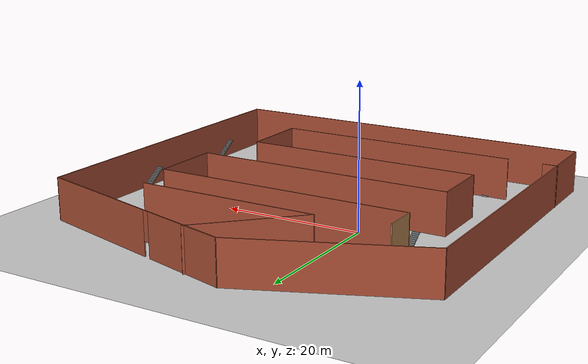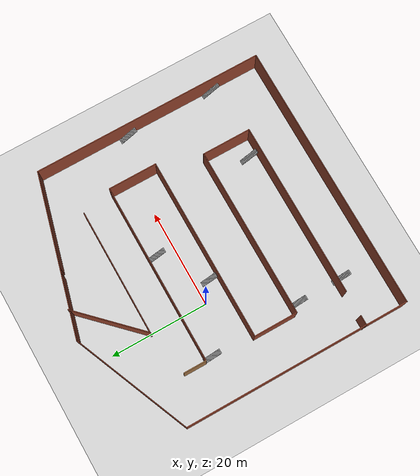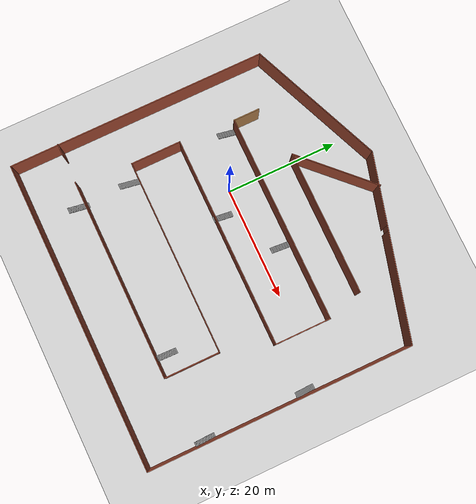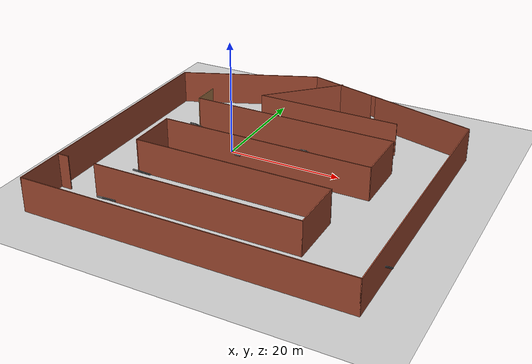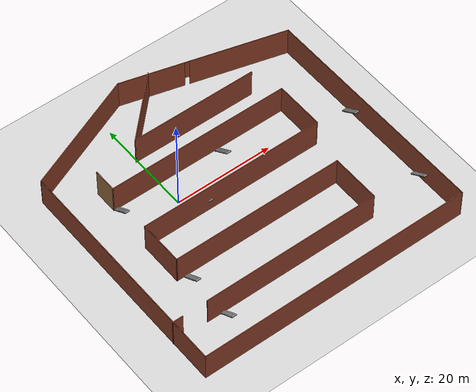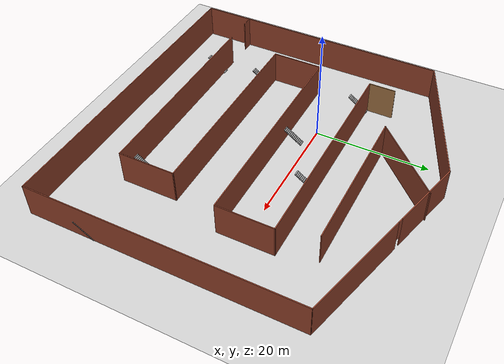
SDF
<sdf version="1.6">
 <world name="default">
  <light name="sun" type="directional">
   <pose>0 0 10 0 -0 0</pose>
   <diffuse>0.8 0.8 0.8 1</diffuse>
   <specular>0.2 0.2 0.2 1</specular>
   <attenuation>
    <range>1000</range>
    <constant>0.9</constant>
    <linear>0.01</linear>
    <quadratic>0.001</quadratic>
   </attenuation>
   <direction>-0.5 0.1 -0.9</direction>
  </light>
  <model name="ground_plane">
   <static>1</static>
   <link name="link">
    <collision name="collision">
     <geometry><plane><normal>0 0 1</normal><size>100 100</size></plane></geometry>
     <surface><friction><ode><mu>100</mu><mu2>50</mu2></ode></friction></surface>
    </collision>
    <visual name="visual">
     <cast_shadows>0</cast_shadows>
     <geometry><plane><normal>0 0 1</normal><size>100 100</size></plane></geometry>
     <material>
      <script><uri>file://media/materials/scripts/gazebo.material</uri><name>Gazebo/Grey</name></script>
     </material>
    </visual>
   </link>
  </model>
  <gravity>0 0 -9.8</gravity>
  <magnetic_field>6e-06 2.3e-05 -4.2e-05</magnetic_field>
  <atmosphere type="adiabatic"/>
  <physics name="default_physics" default="0" type="ode">
   <max_step_size>0.001</max_step_size>
   <real_time_factor>1</real_time_factor>
   <real_time_update_rate>1000</real_time_update_rate>
  </physics>
  <scene><ambient>0.4 0.4 0.4 1</ambient><background>0.7 0.7 0.7 1</background><shadows>1</shadows></scene>
  <spherical_coordinates>
   <surface_model>EARTH_WGS84</surface_model>
   <latitude_deg>0</latitude_deg>
   <longitude_deg>0</longitude_deg>
   <elevation>0</elevation>
   <heading_deg>0</heading_deg>
  </spherical_coordinates>
  <model name="indoor2">
   <pose>9.15043 -3.83345 0 0 -0 0</pose>
   <link name="Stairs_1">
    <visual name="Stairs_1_Visual_0">
     <pose>-17.3524 -19.1277 0.083333 0 -0 0</pose>
     <geometry><box><size>1 0.233333 0.166667</size></box></geometry>
     <material>
      <script><uri>file://media/materials/scripts/gazebo.material</uri><name>Gazebo/Grey</name></script>
      <ambient>1 1 1 1</ambient>
     </material>
     <meta><layer>0</layer></meta>
    </visual>
    <collision name="Stairs_1_Collision_0">
     <geometry><box><size>1 0.233333 0.166667</size></box></geometry>
     <pose>-17.3524 -19.1277 0.083333 0 -0 0</pose>
    </collision>
    <visual name="Stairs_1_Visual_1">
     <pose>-17.3524 -19.361 0.25 0 -0 0</pose>
     <geometry><box><size>1 0.233333 0.166667</size></box></geometry>
     <material>
      <script><uri>file://media/materials/scripts/gazebo.material</uri><name>Gazebo/Grey</name></script>
      <ambient>1 1 1 1</ambient>
     </material>
     <meta><layer>0</layer></meta>
    </visual>
    <collision name="Stairs_1_Collision_1">
     <geometry><box><size>1 0.233333 0.166667</size></box></geometry>
     <pose>-17.3524 -19.361 0.25 0 -0 0</pose>
    </collision>
    <visual name="Stairs_1_Visual_2">
     <pose>-17.3524 -19.5943 0.416667 0 -0 0</pose>
     <geometry><box><size>1 0.233333 0.166667</size></box></geometry>
     <material>
      <script><uri>file://media/materials/scripts/gazebo.material</uri><name>Gazebo/Grey</name></script>
      <ambient>1 1 1 1</ambient>
     </material>
     <meta><layer>0</layer></meta>
    </visual>
    <collision name="Stairs_1_Collision_2">
     <geometry><box><size>1 0.233333 0.166667</size></box></geometry>
     <pose>-17.3524 -19.5943 0.416667 0 -0 0</pose>
    </collision>
    <visual name="Stairs_1_Visual_3">
     <pose>-17.3524 -19.8277 0.583333 0 -0 0</pose>
     <geometry><box><size>1 0.233333 0.166667</size></box></geometry>
     <material>
      <script><uri>file://media/materials/scripts/gazebo.material</uri><name>Gazebo/Grey</name></script>
      <ambient>1 1 1 1</ambient>
     </material>
     <meta><layer>0</layer></meta>
    </visual>
    <collision name="Stairs_1_Collision_3">
     <geometry><box><size>1 0.233333 0.166667</size></box></geometry>
     <pose>-17.3524 -19.8277 0.583333 0 -0 0</pose>
    </collision>
    <visual name="Stairs_1_Visual_4">
     <pose>-17.3524 -20.061 0.75 0 -0 0</pose>
     <geometry><box><size>1 0.233333 0.166667</size></box></geometry>
     <material>
      <script><uri>file://media/materials/scripts/gazebo.material</uri><name>Gazebo/Grey</name></script>
      <ambient>1 1 1 1</ambient>
     </material>
     <meta><layer>0</layer></meta>
    </visual>
    <collision name="Stairs_1_Collision_4">
     <geometry><box><size>1 0.233333 0.166667</size></box></geometry>
     <pose>-17.3524 -20.061 0.75 0 -0 0</pose>
    </collision>
    <visual name="Stairs_1_Visual_5">
     <pose>-17.3524 -20.2943 0.916667 0 -0 0</pose>
     <geometry><box><size>1 0.233333 0.166667</size></box></geometry>
     <material>
      <script><uri>file://media/materials/scripts/gazebo.material</uri><name>Gazebo/Grey</name></script>
      <ambient>1 1 1 1</ambient>
     </material>
     <meta><layer>0</layer></meta>
    </visual>
    <collision name="Stairs_1_Collision_5">
     <geometry><box><size>1 0.233333 0.166667</size></box></geometry>
     <pose>-17.3524 -20.2943 0.916667 0 -0 0</pose>
    </collision>
    <visual name="Stairs_1_Visual_6">
     <pose>-17.3524 -20.5277 1.08333 0 -0 0</pose>
     <geometry><box><size>1 0.233333 0.166667</size></box></geometry>
     <material>
      <script><uri>file://media/materials/scripts/gazebo.material</uri><name>Gazebo/Grey</name></script>
      <ambient>1 1 1 1</ambient>
     </material>
     <meta><layer>0</layer></meta>
    </visual>
    <collision name="Stairs_1_Collision_6">
     <geometry><box><size>1 0.233333 0.166667</size></box></geometry>
     <pose>-17.3524 -20.5277 1.08333 0 -0 0</pose>
    </collision>
    <visual name="Stairs_1_Visual_7">
     <pose>-17.3524 -20.761 1.25 0 -0 0</pose>
     <geometry><box><size>1 0.233333 0.166667</size></box></geometry>
     <material>
      <script><uri>file://media/materials/scripts/gazebo.material</uri><name>Gazebo/Grey</name></script>
      <ambient>1 1 1 1</ambient>
     </material>
     <meta><layer>0</layer></meta>
    </visual>
    <collision name="Stairs_1_Collision_7">
     <geometry><box><size>1 0.233333 0.166667</size></box></geometry>
     <pose>-17.3524 -20.761 1.25 0 -0 0</pose>
    </collision>
    <visual name="Stairs_1_Visual_8">
     <pose>-17.3524 -20.9943 1.41667 0 -0 0</pose>
     <geometry><box><size>1 0.233333 0.166667</size></box></geometry>
     <material>
      <script><uri>file://media/materials/scripts/gazebo.material</uri><name>Gazebo/Grey</name></script>
      <ambient>1 1 1 1</ambient>
     </material>
     <meta><layer>0</layer></meta>
    </visual>
    <collision name="Stairs_1_Collision_8">
     <geometry><box><size>1 0.233333 0.166667</size></box></geometry>
     <pose>-17.3524 -20.9943 1.41667 0 -0 0</pose>
    </collision>
    <visual name="Stairs_1_Visual_9">
     <pose>-17.3524 -21.2277 1.58333 0 -0 0</pose>
     <geometry><box><size>1 0.233333 0.166667</size></box></geometry>
     <material>
      <script><uri>file://media/materials/scripts/gazebo.material</uri><name>Gazebo/Grey</name></script>
      <ambient>1 1 1 1</ambient>
     </material>
     <meta><layer>0</layer></meta>
    </visual>
    <collision name="Stairs_1_Collision_9">
     <geometry><box><size>1 0.233333 0.166667</size></box></geometry>
     <pose>-17.3524 -21.2277 1.58333 0 -0 0</pose>
    </collision>
    <visual name="Stairs_1_Visual_10">
     <pose>-17.3524 -21.461 1.75 0 -0 0</pose>
     <geometry><box><size>1 0.233333 0.166667</size></box></geometry>
     <material>
      <script><uri>file://media/materials/scripts/gazebo.material</uri><name>Gazebo/Grey</name></script>
      <ambient>1 1 1 1</ambient>
     </material>
     <meta><layer>0</layer></meta>
    </visual>
    <collision name="Stairs_1_Collision_10">
     <geometry><box><size>1 0.233333 0.166667</size></box></geometry>
     <pose>-17.3524 -21.461 1.75 0 -0 0</pose>
    </collision>
    <visual name="Stairs_1_Visual_11">
     <pose>-17.3524 -21.6943 1.91667 0 -0 0</pose>
     <geometry><box><size>1 0.233333 0.166667</size></box></geometry>
     <material>
      <script><uri>file://media/materials/scripts/gazebo.material</uri><name>Gazebo/Grey</name></script>
      <ambient>1 1 1 1</ambient>
     </material>
     <meta><layer>0</layer></meta>
    </visual>
    <collision name="Stairs_1_Collision_11">
     <geometry><box><size>1 0.233333 0.166667</size></box></geometry>
     <pose>-17.3524 -21.6943 1.91667 0 -0 0</pose>
    </collision>
    <visual name="Stairs_1_Visual_12">
     <pose>-17.3524 -21.9277 2.08333 0 -0 0</pose>
     <geometry><box><size>1 0.233333 0.166667</size></box></geometry>
     <material>
      <script><uri>file://media/materials/scripts/gazebo.material</uri><name>Gazebo/Grey</name></script>
      <ambient>1 1 1 1</ambient>
     </material>
     <meta><layer>0</layer></meta>
    </visual>
    <collision name="Stairs_1_Collision_12">
     <geometry><box><size>1 0.233333 0.166667</size></box></geometry>
     <pose>-17.3524 -21.9277 2.08333 0 -0 0</pose>
    </collision>
    <visual name="Stairs_1_Visual_13">
     <pose>-17.3524 -22.161 2.25 0 -0 0</pose>
     <geometry><box><size>1 0.233333 0.166667</size></box></geometry>
     <material>
      <script><uri>file://media/materials/scripts/gazebo.material</uri><name>Gazebo/Grey</name></script>
      <ambient>1 1 1 1</ambient>
     </material>
     <meta><layer>0</layer></meta>
    </visual>
    <collision name="Stairs_1_Collision_13">
     <geometry><box><size>1 0.233333 0.166667</size></box></geometry>
     <pose>-17.3524 -22.161 2.25 0 -0 0</pose>
    </collision>
    <visual name="Stairs_1_Visual_14">
     <pose>-17.3524 -22.3943 2.41667 0 -0 0</pose>
     <geometry><box><size>1 0.233333 0.166667</size></box></geometry>
     <material>
      <script><uri>file://media/materials/scripts/gazebo.material</uri><name>Gazebo/Grey</name></script>
      <ambient>1 1 1 1</ambient>
     </material>
     <meta><layer>0</layer></meta>
    </visual>
    <collision name="Stairs_1_Collision_14">
     <geometry><box><size>1 0.233333 0.166667</size></box></geometry>
     <pose>-17.3524 -22.3943 2.41667 0 -0 0</pose>
    </collision>
   </link>
   <link name="Stairs_2">
    <visual name="Stairs_2_Visual_0">
     <pose>27.1992 -16.0338 0.083333 0 -0 0</pose>
     <geometry><box><size>1 0.233333 0.166667</size></box></geometry>
     <material>
      <script><uri>file://media/materials/scripts/gazebo.material</uri><name>Gazebo/Grey</name></script>
      <ambient>1 1 1 1</ambient>
     </material>
     <meta><layer>0</layer></meta>
    </visual>
    <collision name="Stairs_2_Collision_0">
     <geometry><box><size>1 0.233333 0.166667</size></box></geometry>
     <pose>27.1992 -16.0338 0.083333 0 -0 0</pose>
    </collision>
    <visual name="Stairs_2_Visual_1">
     <pose>27.1992 -16.2671 0.25 0 -0 0</pose>
     <geometry><box><size>1 0.233333 0.166667</size></box></geometry>
     <material>
      <script><uri>file://media/materials/scripts/gazebo.material</uri><name>Gazebo/Grey</name></script>
      <ambient>1 1 1 1</ambient>
     </material>
     <meta><layer>0</layer></meta>
    </visual>
    <collision name="Stairs_2_Collision_1">
     <geometry><box><size>1 0.233333 0.166667</size></box></geometry>
     <pose>27.1992 -16.2671 0.25 0 -0 0</pose>
    </collision>
    <visual name="Stairs_2_Visual_2">
     <pose>27.1992 -16.5005 0.416667 0 -0 0</pose>
     <geometry><box><size>1 0.233333 0.166667</size></box></geometry>
     <material>
      <script><uri>file://media/materials/scripts/gazebo.material</uri><name>Gazebo/Grey</name></script>
      <ambient>1 1 1 1</ambient>
     </material>
     <meta><layer>0</layer></meta>
    </visual>
    <collision name="Stairs_2_Collision_2">
     <geometry><box><size>1 0.233333 0.166667</size></box></geometry>
     <pose>27.1992 -16.5005 0.416667 0 -0 0</pose>
    </collision>
    <visual name="Stairs_2_Visual_3">
     <pose>27.1992 -16.7338 0.583333 0 -0 0</pose>
     <geometry><box><size>1 0.233333 0.166667</size></box></geometry>
     <material>
      <script><uri>file://media/materials/scripts/gazebo.material</uri><name>Gazebo/Grey</name></script>
      <ambient>1 1 1 1</ambient>
     </material>
     <meta><layer>0</layer></meta>
    </visual>
    <collision name="Stairs_2_Collision_3">
     <geometry><box><size>1 0.233333 0.166667</size></box></geometry>
     <pose>27.1992 -16.7338 0.583333 0 -0 0</pose>
    </collision>
    <visual name="Stairs_2_Visual_4">
     <pose>27.1992 -16.9671 0.75 0 -0 0</pose>
     <geometry><box><size>1 0.233333 0.166667</size></box></geometry>
     <material>
      <script><uri>file://media/materials/scripts/gazebo.material</uri><name>Gazebo/Grey</name></script>
      <ambient>1 1 1 1</ambient>
     </material>
     <meta><layer>0</layer></meta>
    </visual>
    <collision name="Stairs_2_Collision_4">
     <geometry><box><size>1 0.233333 0.166667</size></box></geometry>
     <pose>27.1992 -16.9671 0.75 0 -0 0</pose>
    </collision>
    <visual name="Stairs_2_Visual_5">
     <pose>27.1992 -17.2005 0.916667 0 -0 0</pose>
     <geometry><box><size>1 0.233333 0.166667</size></box></geometry>
     <material>
      <script><uri>file://media/materials/scripts/gazebo.material</uri><name>Gazebo/Grey</name></script>
      <ambient>1 1 1 1</ambient>
     </material>
     <meta><layer>0</layer></meta>
    </visual>
    <collision name="Stairs_2_Collision_5">
     <geometry><box><size>1 0.233333 0.166667</size></box></geometry>
     <pose>27.1992 -17.2005 0.916667 0 -0 0</pose>
    </collision>
    <visual name="Stairs_2_Visual_6">
     <pose>27.1992 -17.4338 1.08333 0 -0 0</pose>
     <geometry><box><size>1 0.233333 0.166667</size></box></geometry>
     <material>
      <script><uri>file://media/materials/scripts/gazebo.material</uri><name>Gazebo/Grey</name></script>
      <ambient>1 1 1 1</ambient>
     </material>
     <meta><layer>0</layer></meta>
    </visual>
    <collision name="Stairs_2_Collision_6">
     <geometry><box><size>1 0.233333 0.166667</size></box></geometry>
     <pose>27.1992 -17.4338 1.08333 0 -0 0</pose>
    </collision>
    <visual name="Stairs_2_Visual_7">
     <pose>27.1992 -17.6671 1.25 0 -0 0</pose>
     <geometry><box><size>1 0.233333 0.166667</size></box></geometry>
     <material>
      <script><uri>file://media/materials/scripts/gazebo.material</uri><name>Gazebo/Grey</name></script>
      <ambient>1 1 1 1</ambient>
     </material>
     <meta><layer>0</layer></meta>
    </visual>
    <collision name="Stairs_2_Collision_7">
     <geometry><box><size>1 0.233333 0.166667</size></box></geometry>
     <pose>27.1992 -17.6671 1.25 0 -0 0</pose>
    </collision>
    <visual name="Stairs_2_Visual_8">
     <pose>27.1992 -17.9005 1.41667 0 -0 0</pose>
     <geometry><box><size>1 0.233333 0.166667</size></box></geometry>
     <material>
      <script><uri>file://media/materials/scripts/gazebo.material</uri><name>Gazebo/Grey</name></script>
      <ambient>1 1 1 1</ambient>
     </material>
     <meta><layer>0</layer></meta>
    </visual>
    <collision name="Stairs_2_Collision_8">
     <geometry><box><size>1 0.233333 0.166667</size></box></geometry>
     <pose>27.1992 -17.9005 1.41667 0 -0 0</pose>
    </collision>
    <visual name="Stairs_2_Visual_9">
     <pose>27.1992 -18.1338 1.58333 0 -0 0</pose>
     <geometry><box><size>1 0.233333 0.166667</size></box></geometry>
     <material>
      <script><uri>file://media/materials/scripts/gazebo.material</uri><name>Gazebo/Grey</name></script>
      <ambient>1 1 1 1</ambient>
     </material>
     <meta><layer>0</layer></meta>
    </visual>
    <collision name="Stairs_2_Collision_9">
     <geometry><box><size>1 0.233333 0.166667</size></box></geometry>
     <pose>27.1992 -18.1338 1.58333 0 -0 0</pose>
    </collision>
    <visual name="Stairs_2_Visual_10">
     <pose>27.1992 -18.3671 1.75 0 -0 0</pose>
     <geometry><box><size>1 0.233333 0.166667</size></box></geometry>
     <material>
      <script><uri>file://media/materials/scripts/gazebo.material</uri><name>Gazebo/Grey</name></script>
      <ambient>1 1 1 1</ambient>
     </material>
     <meta><layer>0</layer></meta>
    </visual>
    <collision name="Stairs_2_Collision_10">
     <geometry><box><size>1 0.233333 0.166667</size></box></geometry>
     <pose>27.1992 -18.3671 1.75 0 -0 0</pose>
    </collision>
    <visual name="Stairs_2_Visual_11">
     <pose>27.1992 -18.6005 1.91667 0 -0 0</pose>
     <geometry><box><size>1 0.233333 0.166667</size></box></geometry>
     <material>
      <script><uri>file://media/materials/scripts/gazebo.material</uri><name>Gazebo/Grey</name></script>
      <ambient>1 1 1 1</ambient>
     </material>
     <meta><layer>0</layer></meta>
    </visual>
    <collision name="Stairs_2_Collision_11">
     <geometry><box><size>1 0.233333 0.166667</size></box></geometry>
     <pose>27.1992 -18.6005 1.91667 0 -0 0</pose>
    </collision>
    <visual name="Stairs_2_Visual_12">
     <pose>27.1992 -18.8338 2.08333 0 -0 0</pose>
     <geometry><box><size>1 0.233333 0.166667</size></box></geometry>
     <material>
      <script><uri>file://media/materials/scripts/gazebo.material</uri><name>Gazebo/Grey</name></script>
      <ambient>1 1 1 1</ambient>
     </material>
     <meta><layer>0</layer></meta>
    </visual>
    <collision name="Stairs_2_Collision_12">
     <geometry><box><size>1 0.233333 0.166667</size></box></geometry>
     <pose>27.1992 -18.8338 2.08333 0 -0 0</pose>
    </collision>
    <visual name="Stairs_2_Visual_13">
     <pose>27.1992 -19.0671 2.25 0 -0 0</pose>
     <geometry><box><size>1 0.233333 0.166667</size></box></geometry>
     <material>
      <script><uri>file://media/materials/scripts/gazebo.material</uri><name>Gazebo/Grey</name></script>
      <ambient>1 1 1 1</ambient>
     </material>
     <meta><layer>0</layer></meta>
    </visual>
    <collision name="Stairs_2_Collision_13">
     <geometry><box><size>1 0.233333 0.166667</size></box></geometry>
     <pose>27.1992 -19.0671 2.25 0 -0 0</pose>
    </collision>
    <visual name="Stairs_2_Visual_14">
     <pose>27.1992 -19.3005 2.41667 0 -0 0</pose>
     <geometry><box><size>1 0.233333 0.166667</size></box></geometry>
     <material>
      <script><uri>file://media/materials/scripts/gazebo.material</uri><name>Gazebo/Grey</name></script>
      <ambient>1 1 1 1</ambient>
     </material>
     <meta><layer>0</layer></meta>
    </visual>
    <collision name="Stairs_2_Collision_14">
     <geometry><box><size>1 0.233333 0.166667</size></box></geometry>
     <pose>27.1992 -19.3005 2.41667 0 -0 0</pose>
    </collision>
   </link>
   <link name="Stairs_3">
    <visual name="Stairs_3_Visual_0">
     <pose>26.9517 2.40562 0.083333 0 -0 0</pose>
     <geometry><box><size>1 0.233333 0.166667</size></box></geometry>
     <material>
      <script><uri>file://media/materials/scripts/gazebo.material</uri><name>Gazebo/Grey</name></script>
      <ambient>1 1 1 1</ambient>
     </material>
     <meta><layer>0</layer></meta>
    </visual>
    <collision name="Stairs_3_Collision_0">
     <geometry><box><size>1 0.233333 0.166667</size></box></geometry>
     <pose>26.9517 2.40562 0.083333 0 -0 0</pose>
    </collision>
    <visual name="Stairs_3_Visual_1">
     <pose>26.9517 2.17229 0.25 0 -0 0</pose>
     <geometry><box><size>1 0.233333 0.166667</size></box></geometry>
     <material>
      <script><uri>file://media/materials/scripts/gazebo.material</uri><name>Gazebo/Grey</name></script>
      <ambient>1 1 1 1</ambient>
     </material>
     <meta><layer>0</layer></meta>
    </visual>
    <collision name="Stairs_3_Collision_1">
     <geometry><box><size>1 0.233333 0.166667</size></box></geometry>
     <pose>26.9517 2.17229 0.25 0 -0 0</pose>
    </collision>
    <visual name="Stairs_3_Visual_2">
     <pose>26.9517 1.93895 0.416667 0 -0 0</pose>
     <geometry><box><size>1 0.233333 0.166667</size></box></geometry>
     <material>
      <script><uri>file://media/materials/scripts/gazebo.material</uri><name>Gazebo/Grey</name></script>
      <ambient>1 1 1 1</ambient>
     </material>
     <meta><layer>0</layer></meta>
    </visual>
    <collision name="Stairs_3_Collision_2">
     <geometry><box><size>1 0.233333 0.166667</size></box></geometry>
     <pose>26.9517 1.93895 0.416667 0 -0 0</pose>
    </collision>
    <visual name="Stairs_3_Visual_3">
     <pose>26.9517 1.70562 0.583333 0 -0 0</pose>
     <geometry><box><size>1 0.233333 0.166667</size></box></geometry>
     <material>
      <script><uri>file://media/materials/scripts/gazebo.material</uri><name>Gazebo/Grey</name></script>
      <ambient>1 1 1 1</ambient>
     </material>
     <meta><layer>0</layer></meta>
    </visual>
    <collision name="Stairs_3_Collision_3">
     <geometry><box><size>1 0.233333 0.166667</size></box></geometry>
     <pose>26.9517 1.70562 0.583333 0 -0 0</pose>
    </collision>
    <visual name="Stairs_3_Visual_4">
     <pose>26.9517 1.47229 0.75 0 -0 0</pose>
     <geometry><box><size>1 0.233333 0.166667</size></box></geometry>
     <material>
      <script><uri>file://media/materials/scripts/gazebo.material</uri><name>Gazebo/Grey</name></script>
      <ambient>1 1 1 1</ambient>
     </material>
     <meta><layer>0</layer></meta>
    </visual>
    <collision name="Stairs_3_Collision_4">
     <geometry><box><size>1 0.233333 0.166667</size></box></geometry>
     <pose>26.9517 1.47229 0.75 0 -0 0</pose>
    </collision>
    <visual name="Stairs_3_Visual_5">
     <pose>26.9517 1.23895 0.916667 0 -0 0</pose>
     <geometry><box><size>1 0.233333 0.166667</size></box></geometry>
     <material>
      <script><uri>file://media/materials/scripts/gazebo.material</uri><name>Gazebo/Grey</name></script>
      <ambient>1 1 1 1</ambient>
     </material>
     <meta><layer>0</layer></meta>
    </visual>
    <collision name="Stairs_3_Collision_5">
     <geometry><box><size>1 0.233333 0.166667</size></box></geometry>
     <pose>26.9517 1.23895 0.916667 0 -0 0</pose>
    </collision>
    <visual name="Stairs_3_Visual_6">
     <pose>26.9517 1.00562 1.08333 0 -0 0</pose>
     <geometry><box><size>1 0.233333 0.166667</size></box></geometry>
     <material>
      <script><uri>file://media/materials/scripts/gazebo.material</uri><name>Gazebo/Grey</name></script>
      <ambient>1 1 1 1</ambient>
     </material>
     <meta><layer>0</layer></meta>
    </visual>
    <collision name="Stairs_3_Collision_6">
     <geometry><box><size>1 0.233333 0.166667</size></box></geometry>
     <pose>26.9517 1.00562 1.08333 0 -0 0</pose>
    </collision>
    <visual name="Stairs_3_Visual_7">
     <pose>26.9517 0.772287 1.25 0 -0 0</pose>
     <geometry><box><size>1 0.233333 0.166667</size></box></geometry>
     <material>
      <script><uri>file://media/materials/scripts/gazebo.material</uri><name>Gazebo/Grey</name></script>
      <ambient>1 1 1 1</ambient>
     </material>
     <meta><layer>0</layer></meta>
    </visual>
    <collision name="Stairs_3_Collision_7">
     <geometry><box><size>1 0.233333 0.166667</size></box></geometry>
     <pose>26.9517 0.772287 1.25 0 -0 0</pose>
    </collision>
    <visual name="Stairs_3_Visual_8">
     <pose>26.9517 0.538954 1.41667 0 -0 0</pose>
     <geometry><box><size>1 0.233333 0.166667</size></box></geometry>
     <material>
      <script><uri>file://media/materials/scripts/gazebo.material</uri><name>Gazebo/Grey</name></script>
      <ambient>1 1 1 1</ambient>
     </material>
     <meta><layer>0</layer></meta>
    </visual>
    <collision name="Stairs_3_Collision_8">
     <geometry><box><size>1 0.233333 0.166667</size></box></geometry>
     <pose>26.9517 0.538954 1.41667 0 -0 0</pose>
    </collision>
    <visual name="Stairs_3_Visual_9">
     <pose>26.9517 0.30562 1.58333 0 -0 0</pose>
     <geometry><box><size>1 0.233333 0.166667</size></box></geometry>
     <material>
      <script><uri>file://media/materials/scripts/gazebo.material</uri><name>Gazebo/Grey</name></script>
      <ambient>1 1 1 1</ambient>
     </material>
     <meta><layer>0</layer></meta>
    </visual>
    <collision name="Stairs_3_Collision_9">
     <geometry><box><size>1 0.233333 0.166667</size></box></geometry>
     <pose>26.9517 0.30562 1.58333 0 -0 0</pose>
    </collision>
    <visual name="Stairs_3_Visual_10">
     <pose>26.9517 0.072287 1.75 0 -0 0</pose>
     <geometry><box><size>1 0.233333 0.166667</size></box></geometry>
     <material>
      <script><uri>file://media/materials/scripts/gazebo.material</uri><name>Gazebo/Grey</name></script>
      <ambient>1 1 1 1</ambient>
     </material>
     <meta><layer>0</layer></meta>
    </visual>
    <collision name="Stairs_3_Collision_10">
     <geometry><box><size>1 0.233333 0.166667</size></box></geometry>
     <pose>26.9517 0.072287 1.75 0 -0 0</pose>
    </collision>
    <visual name="Stairs_3_Visual_11">
     <pose>26.9517 -0.161047 1.91667 0 -0 0</pose>
     <geometry><box><size>1 0.233333 0.166667</size></box></geometry>
     <material>
      <script><uri>file://media/materials/scripts/gazebo.material</uri><name>Gazebo/Grey</name></script>
      <ambient>1 1 1 1</ambient>
     </material>
     <meta><layer>0</layer></meta>
    </visual>
    <collision name="Stairs_3_Collision_11">
     <geometry><box><size>1 0.233333 0.166667</size></box></geometry>
     <pose>26.9517 -0.161047 1.91667 0 -0 0</pose>
    </collision>
    <visual name="Stairs_3_Visual_12">
     <pose>26.9517 -0.39438 2.08333 0 -0 0</pose>
     <geometry><box><size>1 0.233333 0.166667</size></box></geometry>
     <material>
      <script><uri>file://media/materials/scripts/gazebo.material</uri><name>Gazebo/Grey</name></script>
      <ambient>1 1 1 1</ambient>
     </material>
     <meta><layer>0</layer></meta>
    </visual>
    <collision name="Stairs_3_Collision_12">
     <geometry><box><size>1 0.233333 0.166667</size></box></geometry>
     <pose>26.9517 -0.39438 2.08333 0 -0 0</pose>
    </collision>
    <visual name="Stairs_3_Visual_13">
     <pose>26.9517 -0.627713 2.25 0 -0 0</pose>
     <geometry><box><size>1 0.233333 0.166667</size></box></geometry>
     <material>
      <script><uri>file://media/materials/scripts/gazebo.material</uri><name>Gazebo/Grey</name></script>
      <ambient>1 1 1 1</ambient>
     </material>
     <meta><layer>0</layer></meta>
    </visual>
    <collision name="Stairs_3_Collision_13">
     <geometry><box><size>1 0.233333 0.166667</size></box></geometry>
     <pose>26.9517 -0.627713 2.25 0 -0 0</pose>
    </collision>
    <visual name="Stairs_3_Visual_14">
     <pose>26.9517 -0.861046 2.41667 0 -0 0</pose>
     <geometry><box><size>1 0.233333 0.166667</size></box></geometry>
     <material>
      <script><uri>file://media/materials/scripts/gazebo.material</uri><name>Gazebo/Grey</name></script>
      <ambient>1 1 1 1</ambient>
     </material>
     <meta><layer>0</layer></meta>
    </visual>
    <collision name="Stairs_3_Collision_14">
     <geometry><box><size>1 0.233333 0.166667</size></box></geometry>
     <pose>26.9517 -0.861046 2.41667 0 -0 0</pose>
    </collision>
   </link>
   <link name="Stairs_4">
    <visual name="Stairs_4_Visual_0">
     <pose>3.43833 9.08836 0.083333 0 -0 0</pose>
     <geometry><box><size>1 0.233333 0.166667</size></box></geometry>
     <material>
      <script><uri>file://media/materials/scripts/gazebo.material</uri><name>Gazebo/Grey</name></script>
      <ambient>1 1 1 1</ambient>
     </material>
     <meta><layer>0</layer></meta>
    </visual>
    <collision name="Stairs_4_Collision_0">
     <geometry><box><size>1 0.233333 0.166667</size></box></geometry>
     <pose>3.43833 9.08836 0.083333 0 -0 0</pose>
    </collision>
    <visual name="Stairs_4_Visual_1">
     <pose>3.43833 8.85503 0.25 0 -0 0</pose>
     <geometry><box><size>1 0.233333 0.166667</size></box></geometry>
     <material>
      <script><uri>file://media/materials/scripts/gazebo.material</uri><name>Gazebo/Grey</name></script>
      <ambient>1 1 1 1</ambient>
     </material>
     <meta><layer>0</layer></meta>
    </visual>
    <collision name="Stairs_4_Collision_1">
     <geometry><box><size>1 0.233333 0.166667</size></box></geometry>
     <pose>3.43833 8.85503 0.25 0 -0 0</pose>
    </collision>
    <visual name="Stairs_4_Visual_2">
     <pose>3.43833 8.6217 0.416667 0 -0 0</pose>
     <geometry><box><size>1 0.233333 0.166667</size></box></geometry>
     <material>
      <script><uri>file://media/materials/scripts/gazebo.material</uri><name>Gazebo/Grey</name></script>
      <ambient>1 1 1 1</ambient>
     </material>
     <meta><layer>0</layer></meta>
    </visual>
    <collision name="Stairs_4_Collision_2">
     <geometry><box><size>1 0.233333 0.166667</size></box></geometry>
     <pose>3.43833 8.6217 0.416667 0 -0 0</pose>
    </collision>
    <visual name="Stairs_4_Visual_3">
     <pose>3.43833 8.38837 0.583333 0 -0 0</pose>
     <geometry><box><size>1 0.233333 0.166667</size></box></geometry>
     <material>
      <script><uri>file://media/materials/scripts/gazebo.material</uri><name>Gazebo/Grey</name></script>
      <ambient>1 1 1 1</ambient>
     </material>
     <meta><layer>0</layer></meta>
    </visual>
    <collision name="Stairs_4_Collision_3">
     <geometry><box><size>1 0.233333 0.166667</size></box></geometry>
     <pose>3.43833 8.38837 0.583333 0 -0 0</pose>
    </collision>
    <visual name="Stairs_4_Visual_4">
     <pose>3.43833 8.15503 0.75 0 -0 0</pose>
     <geometry><box><size>1 0.233333 0.166667</size></box></geometry>
     <material>
      <script><uri>file://media/materials/scripts/gazebo.material</uri><name>Gazebo/Grey</name></script>
      <ambient>1 1 1 1</ambient>
     </material>
     <meta><layer>0</layer></meta>
    </visual>
    <collision name="Stairs_4_Collision_4">
     <geometry><box><size>1 0.233333 0.166667</size></box></geometry>
     <pose>3.43833 8.15503 0.75 0 -0 0</pose>
    </collision>
    <visual name="Stairs_4_Visual_5">
     <pose>3.43833 7.9217 0.916667 0 -0 0</pose>
     <geometry><box><size>1 0.233333 0.166667</size></box></geometry>
     <material>
      <script><uri>file://media/materials/scripts/gazebo.material</uri><name>Gazebo/Grey</name></script>
      <ambient>1 1 1 1</ambient>
     </material>
     <meta><layer>0</layer></meta>
    </visual>
    <collision name="Stairs_4_Collision_5">
     <geometry><box><size>1 0.233333 0.166667</size></box></geometry>
     <pose>3.43833 7.9217 0.916667 0 -0 0</pose>
    </collision>
    <visual name="Stairs_4_Visual_6">
     <pose>3.43833 7.68837 1.08333 0 -0 0</pose>
     <geometry><box><size>1 0.233333 0.166667</size></box></geometry>
     <material>
      <script><uri>file://media/materials/scripts/gazebo.material</uri><name>Gazebo/Grey</name></script>
      <ambient>1 1 1 1</ambient>
     </material>
     <meta><layer>0</layer></meta>
    </visual>
    <collision name="Stairs_4_Collision_6">
     <geometry><box><size>1 0.233333 0.166667</size></box></geometry>
     <pose>3.43833 7.68837 1.08333 0 -0 0</pose>
    </collision>
    <visual name="Stairs_4_Visual_7">
     <pose>3.43833 7.45503 1.25 0 -0 0</pose>
     <geometry><box><size>1 0.233333 0.166667</size></box></geometry>
     <material>
      <script><uri>file://media/materials/scripts/gazebo.material</uri><name>Gazebo/Grey</name></script>
      <ambient>1 1 1 1</ambient>
     </material>
     <meta><layer>0</layer></meta>
    </visual>
    <collision name="Stairs_4_Collision_7">
     <geometry><box><size>1 0.233333 0.166667</size></box></geometry>
     <pose>3.43833 7.45503 1.25 0 -0 0</pose>
    </collision>
    <visual name="Stairs_4_Visual_8">
     <pose>3.43833 7.2217 1.41667 0 -0 0</pose>
     <geometry><box><size>1 0.233333 0.166667</size></box></geometry>
     <material>
      <script><uri>file://media/materials/scripts/gazebo.material</uri><name>Gazebo/Grey</name></script>
      <ambient>1 1 1 1</ambient>
     </material>
     <meta><layer>0</layer></meta>
    </visual>
    <collision name="Stairs_4_Collision_8">
     <geometry><box><size>1 0.233333 0.166667</size></box></geometry>
     <pose>3.43833 7.2217 1.41667 0 -0 0</pose>
    </collision>
    <visual name="Stairs_4_Visual_9">
     <pose>3.43833 6.98836 1.58333 0 -0 0</pose>
     <geometry><box><size>1 0.233333 0.166667</size></box></geometry>
     <material>
      <script><uri>file://media/materials/scripts/gazebo.material</uri><name>Gazebo/Grey</name></script>
      <ambient>1 1 1 1</ambient>
     </material>
     <meta><layer>0</layer></meta>
    </visual>
    <collision name="Stairs_4_Collision_9">
     <geometry><box><size>1 0.233333 0.166667</size></box></geometry>
     <pose>3.43833 6.98836 1.58333 0 -0 0</pose>
    </collision>
    <visual name="Stairs_4_Visual_10">
     <pose>3.43833 6.75503 1.75 0 -0 0</pose>
     <geometry><box><size>1 0.233333 0.166667</size></box></geometry>
     <material>
      <script><uri>file://media/materials/scripts/gazebo.material</uri><name>Gazebo/Grey</name></script>
      <ambient>1 1 1 1</ambient>
     </material>
     <meta><layer>0</layer></meta>
    </visual>
    <collision name="Stairs_4_Collision_10">
     <geometry><box><size>1 0.233333 0.166667</size></box></geometry>
     <pose>3.43833 6.75503 1.75 0 -0 0</pose>
    </collision>
    <visual name="Stairs_4_Visual_11">
     <pose>3.43833 6.5217 1.91667 0 -0 0</pose>
     <geometry><box><size>1 0.233333 0.166667</size></box></geometry>
     <material>
      <script><uri>file://media/materials/scripts/gazebo.material</uri><name>Gazebo/Grey</name></script>
      <ambient>1 1 1 1</ambient>
     </material>
     <meta><layer>0</layer></meta>
    </visual>
    <collision name="Stairs_4_Collision_11">
     <geometry><box><size>1 0.233333 0.166667</size></box></geometry>
     <pose>3.43833 6.5217 1.91667 0 -0 0</pose>
    </collision>
    <visual name="Stairs_4_Visual_12">
     <pose>3.43833 6.28836 2.08333 0 -0 0</pose>
     <geometry><box><size>1 0.233333 0.166667</size></box></geometry>
     <material>
      <script><uri>file://media/materials/scripts/gazebo.material</uri><name>Gazebo/Grey</name></script>
      <ambient>1 1 1 1</ambient>
     </material>
     <meta><layer>0</layer></meta>
    </visual>
    <collision name="Stairs_4_Collision_12">
     <geometry><box><size>1 0.233333 0.166667</size></box></geometry>
     <pose>3.43833 6.28836 2.08333 0 -0 0</pose>
    </collision>
    <visual name="Stairs_4_Visual_13">
     <pose>3.43833 6.05503 2.25 0 -0 0</pose>
     <geometry><box><size>1 0.233333 0.166667</size></box></geometry>
     <material>
      <script><uri>file://media/materials/scripts/gazebo.material</uri><name>Gazebo/Grey</name></script>
      <ambient>1 1 1 1</ambient>
     </material>
     <meta><layer>0</layer></meta>
    </visual>
    <collision name="Stairs_4_Collision_13">
     <geometry><box><size>1 0.233333 0.166667</size></box></geometry>
     <pose>3.43833 6.05503 2.25 0 -0 0</pose>
    </collision>
    <visual name="Stairs_4_Visual_14">
     <pose>3.43833 5.8217 2.41667 0 -0 0</pose>
     <geometry><box><size>1 0.233333 0.166667</size></box></geometry>
     <material>
      <script><uri>file://media/materials/scripts/gazebo.material</uri><name>Gazebo/Grey</name></script>
      <ambient>1 1 1 1</ambient>
     </material>
     <meta><layer>0</layer></meta>
    </visual>
    <collision name="Stairs_4_Collision_14">
     <geometry><box><size>1 0.233333 0.166667</size></box></geometry>
     <pose>3.43833 5.8217 2.41667 0 -0 0</pose>
    </collision>
   </link>
   <link name="Stairs_5">
    <visual name="Stairs_5_Visual_0">
     <pose>-5.472 2.52937 0.083333 0 -0 0</pose>
     <geometry><box><size>1 0.233333 0.166667</size></box></geometry>
     <material>
      <script><uri>file://media/materials/scripts/gazebo.material</uri><name>Gazebo/Grey</name></script>
      <ambient>1 1 1 1</ambient>
     </material>
     <meta><layer>0</layer></meta>
    </visual>
    <collision name="Stairs_5_Collision_0">
     <geometry><box><size>1 0.233333 0.166667</size></box></geometry>
     <pose>-5.472 2.52937 0.083333 0 -0 0</pose>
    </collision>
    <visual name="Stairs_5_Visual_1">
     <pose>-5.472 2.29604 0.25 0 -0 0</pose>
     <geometry><box><size>1 0.233333 0.166667</size></box></geometry>
     <material>
      <script><uri>file://media/materials/scripts/gazebo.material</uri><name>Gazebo/Grey</name></script>
      <ambient>1 1 1 1</ambient>
     </material>
     <meta><layer>0</layer></meta>
    </visual>
    <collision name="Stairs_5_Collision_1">
     <geometry><box><size>1 0.233333 0.166667</size></box></geometry>
     <pose>-5.472 2.29604 0.25 0 -0 0</pose>
    </collision>
    <visual name="Stairs_5_Visual_2">
     <pose>-5.472 2.06271 0.416667 0 -0 0</pose>
     <geometry><box><size>1 0.233333 0.166667</size></box></geometry>
     <material>
      <script><uri>file://media/materials/scripts/gazebo.material</uri><name>Gazebo/Grey</name></script>
      <ambient>1 1 1 1</ambient>
     </material>
     <meta><layer>0</layer></meta>
    </visual>
    <collision name="Stairs_5_Collision_2">
     <geometry><box><size>1 0.233333 0.166667</size></box></geometry>
     <pose>-5.472 2.06271 0.416667 0 -0 0</pose>
    </collision>
    <visual name="Stairs_5_Visual_3">
     <pose>-5.472 1.82937 0.583333 0 -0 0</pose>
     <geometry><box><size>1 0.233333 0.166667</size></box></geometry>
     <material>
      <script><uri>file://media/materials/scripts/gazebo.material</uri><name>Gazebo/Grey</name></script>
      <ambient>1 1 1 1</ambient>
     </material>
     <meta><layer>0</layer></meta>
    </visual>
    <collision name="Stairs_5_Collision_3">
     <geometry><box><size>1 0.233333 0.166667</size></box></geometry>
     <pose>-5.472 1.82937 0.583333 0 -0 0</pose>
    </collision>
    <visual name="Stairs_5_Visual_4">
     <pose>-5.472 1.59604 0.75 0 -0 0</pose>
     <geometry><box><size>1 0.233333 0.166667</size></box></geometry>
     <material>
      <script><uri>file://media/materials/scripts/gazebo.material</uri><name>Gazebo/Grey</name></script>
      <ambient>1 1 1 1</ambient>
     </material>
     <meta><layer>0</layer></meta>
    </visual>
    <collision name="Stairs_5_Collision_4">
     <geometry><box><size>1 0.233333 0.166667</size></box></geometry>
     <pose>-5.472 1.59604 0.75 0 -0 0</pose>
    </collision>
    <visual name="Stairs_5_Visual_5">
     <pose>-5.472 1.36271 0.916667 0 -0 0</pose>
     <geometry><box><size>1 0.233333 0.166667</size></box></geometry>
     <material>
      <script><uri>file://media/materials/scripts/gazebo.material</uri><name>Gazebo/Grey</name></script>
      <ambient>1 1 1 1</ambient>
     </material>
     <meta><layer>0</layer></meta>
    </visual>
    <collision name="Stairs_5_Collision_5">
     <geometry><box><size>1 0.233333 0.166667</size></box></geometry>
     <pose>-5.472 1.36271 0.916667 0 -0 0</pose>
    </collision>
    <visual name="Stairs_5_Visual_6">
     <pose>-5.472 1.12938 1.08333 0 -0 0</pose>
     <geometry><box><size>1 0.233333 0.166667</size></box></geometry>
     <material>
      <script><uri>file://media/materials/scripts/gazebo.material</uri><name>Gazebo/Grey</name></script>
      <ambient>1 1 1 1</ambient>
     </material>
     <meta><layer>0</layer></meta>
    </visual>
    <collision name="Stairs_5_Collision_6">
     <geometry><box><size>1 0.233333 0.166667</size></box></geometry>
     <pose>-5.472 1.12938 1.08333 0 -0 0</pose>
    </collision>
    <visual name="Stairs_5_Visual_7">
     <pose>-5.472 0.896041 1.25 0 -0 0</pose>
     <geometry><box><size>1 0.233333 0.166667</size></box></geometry>
     <material>
      <script><uri>file://media/materials/scripts/gazebo.material</uri><name>Gazebo/Grey</name></script>
      <ambient>1 1 1 1</ambient>
     </material>
     <meta><layer>0</layer></meta>
    </visual>
    <collision name="Stairs_5_Collision_7">
     <geometry><box><size>1 0.233333 0.166667</size></box></geometry>
     <pose>-5.472 0.896041 1.25 0 -0 0</pose>
    </collision>
    <visual name="Stairs_5_Visual_8">
     <pose>-5.472 0.662708 1.41667 0 -0 0</pose>
     <geometry><box><size>1 0.233333 0.166667</size></box></geometry>
     <material>
      <script><uri>file://media/materials/scripts/gazebo.material</uri><name>Gazebo/Grey</name></script>
      <ambient>1 1 1 1</ambient>
     </material>
     <meta><layer>0</layer></meta>
    </visual>
    <collision name="Stairs_5_Collision_8">
     <geometry><box><size>1 0.233333 0.166667</size></box></geometry>
     <pose>-5.472 0.662708 1.41667 0 -0 0</pose>
    </collision>
    <visual name="Stairs_5_Visual_9">
     <pose>-5.472 0.429375 1.58333 0 -0 0</pose>
     <geometry><box><size>1 0.233333 0.166667</size></box></geometry>
     <material>
      <script><uri>file://media/materials/scripts/gazebo.material</uri><name>Gazebo/Grey</name></script>
      <ambient>1 1 1 1</ambient>
     </material>
     <meta><layer>0</layer></meta>
    </visual>
    <collision name="Stairs_5_Collision_9">
     <geometry><box><size>1 0.233333 0.166667</size></box></geometry>
     <pose>-5.472 0.429375 1.58333 0 -0 0</pose>
    </collision>
    <visual name="Stairs_5_Visual_10">
     <pose>-5.472 0.196041 1.75 0 -0 0</pose>
     <geometry><box><size>1 0.233333 0.166667</size></box></geometry>
     <material>
      <script><uri>file://media/materials/scripts/gazebo.material</uri><name>Gazebo/Grey</name></script>
      <ambient>1 1 1 1</ambient>
     </material>
     <meta><layer>0</layer></meta>
    </visual>
    <collision name="Stairs_5_Collision_10">
     <geometry><box><size>1 0.233333 0.166667</size></box></geometry>
     <pose>-5.472 0.196041 1.75 0 -0 0</pose>
    </collision>
    <visual name="Stairs_5_Visual_11">
     <pose>-5.472 -0.037292 1.91667 0 -0 0</pose>
     <geometry><box><size>1 0.233333 0.166667</size></box></geometry>
     <material>
      <script><uri>file://media/materials/scripts/gazebo.material</uri><name>Gazebo/Grey</name></script>
      <ambient>1 1 1 1</ambient>
     </material>
     <meta><layer>0</layer></meta>
    </visual>
    <collision name="Stairs_5_Collision_11">
     <geometry><box><size>1 0.233333 0.166667</size></box></geometry>
     <pose>-5.472 -0.037292 1.91667 0 -0 0</pose>
    </collision>
    <visual name="Stairs_5_Visual_12">
     <pose>-5.472 -0.270625 2.08333 0 -0 0</pose>
     <geometry><box><size>1 0.233333 0.166667</size></box></geometry>
     <material>
      <script><uri>file://media/materials/scripts/gazebo.material</uri><name>Gazebo/Grey</name></script>
      <ambient>1 1 1 1</ambient>
     </material>
     <meta><layer>0</layer></meta>
    </visual>
    <collision name="Stairs_5_Collision_12">
     <geometry><box><size>1 0.233333 0.166667</size></box></geometry>
     <pose>-5.472 -0.270625 2.08333 0 -0 0</pose>
    </collision>
    <visual name="Stairs_5_Visual_13">
     <pose>-5.472 -0.503959 2.25 0 -0 0</pose>
     <geometry><box><size>1 0.233333 0.166667</size></box></geometry>
     <material>
      <script><uri>file://media/materials/scripts/gazebo.material</uri><name>Gazebo/Grey</name></script>
      <ambient>1 1 1 1</ambient>
     </material>
     <meta><layer>0</layer></meta>
    </visual>
    <collision name="Stairs_5_Collision_13">
     <geometry><box><size>1 0.233333 0.166667</size></box></geometry>
     <pose>-5.472 -0.503959 2.25 0 -0 0</pose>
    </collision>
    <visual name="Stairs_5_Visual_14">
     <pose>-5.472 -0.737292 2.41667 0 -0 0</pose>
     <geometry><box><size>1 0.233333 0.166667</size></box></geometry>
     <material>
      <script><uri>file://media/materials/scripts/gazebo.material</uri><name>Gazebo/Grey</name></script>
      <ambient>1 1 1 1</ambient>
     </material>
     <meta><layer>0</layer></meta>
    </visual>
    <collision name="Stairs_5_Collision_14">
     <geometry><box><size>1 0.233333 0.166667</size></box></geometry>
     <pose>-5.472 -0.737292 2.41667 0 -0 0</pose>
    </collision>
   </link>
   <link name="Stairs_6">
    <visual name="Stairs_6_Visual_0">
     <pose>-18.3425 9.33587 0.083333 0 -0 0</pose>
     <geometry><box><size>1 0.233333 0.166667</size></box></geometry>
     <material>
      <script><uri>file://media/materials/scripts/gazebo.material</uri><name>Gazebo/Grey</name></script>
      <ambient>1 1 1 1</ambient>
     </material>
     <meta><layer>0</layer></meta>
    </visual>
    <collision name="Stairs_6_Collision_0">
     <geometry><box><size>1 0.233333 0.166667</size></box></geometry>
     <pose>-18.3425 9.33587 0.083333 0 -0 0</pose>
    </collision>
    <visual name="Stairs_6_Visual_1">
     <pose>-18.3425 9.10254 0.25 0 -0 0</pose>
     <geometry><box><size>1 0.233333 0.166667</size></box></geometry>
     <material>
      <script><uri>file://media/materials/scripts/gazebo.material</uri><name>Gazebo/Grey</name></script>
      <ambient>1 1 1 1</ambient>
     </material>
     <meta><layer>0</layer></meta>
    </visual>
    <collision name="Stairs_6_Collision_1">
     <geometry><box><size>1 0.233333 0.166667</size></box></geometry>
     <pose>-18.3425 9.10254 0.25 0 -0 0</pose>
    </collision>
    <visual name="Stairs_6_Visual_2">
     <pose>-18.3425 8.86921 0.416667 0 -0 0</pose>
     <geometry><box><size>1 0.233333 0.166667</size></box></geometry>
     <material>
      <script><uri>file://media/materials/scripts/gazebo.material</uri><name>Gazebo/Grey</name></script>
      <ambient>1 1 1 1</ambient>
     </material>
     <meta><layer>0</layer></meta>
    </visual>
    <collision name="Stairs_6_Collision_2">
     <geometry><box><size>1 0.233333 0.166667</size></box></geometry>
     <pose>-18.3425 8.86921 0.416667 0 -0 0</pose>
    </collision>
    <visual name="Stairs_6_Visual_3">
     <pose>-18.3425 8.63587 0.583333 0 -0 0</pose>
     <geometry><box><size>1 0.233333 0.166667</size></box></geometry>
     <material>
      <script><uri>file://media/materials/scripts/gazebo.material</uri><name>Gazebo/Grey</name></script>
      <ambient>1 1 1 1</ambient>
     </material>
     <meta><layer>0</layer></meta>
    </visual>
    <collision name="Stairs_6_Collision_3">
     <geometry><box><size>1 0.233333 0.166667</size></box></geometry>
     <pose>-18.3425 8.63587 0.583333 0 -0 0</pose>
    </collision>
    <visual name="Stairs_6_Visual_4">
     <pose>-18.3425 8.40254 0.75 0 -0 0</pose>
     <geometry><box><size>1 0.233333 0.166667</size></box></geometry>
     <material>
      <script><uri>file://media/materials/scripts/gazebo.material</uri><name>Gazebo/Grey</name></script>
      <ambient>1 1 1 1</ambient>
     </material>
     <meta><layer>0</layer></meta>
    </visual>
    <collision name="Stairs_6_Collision_4">
     <geometry><box><size>1 0.233333 0.166667</size></box></geometry>
     <pose>-18.3425 8.40254 0.75 0 -0 0</pose>
    </collision>
    <visual name="Stairs_6_Visual_5">
     <pose>-18.3425 8.16921 0.916667 0 -0 0</pose>
     <geometry><box><size>1 0.233333 0.166667</size></box></geometry>
     <material>
      <script><uri>file://media/materials/scripts/gazebo.material</uri><name>Gazebo/Grey</name></script>
      <ambient>1 1 1 1</ambient>
     </material>
     <meta><layer>0</layer></meta>
    </visual>
    <collision name="Stairs_6_Collision_5">
     <geometry><box><size>1 0.233333 0.166667</size></box></geometry>
     <pose>-18.3425 8.16921 0.916667 0 -0 0</pose>
    </collision>
    <visual name="Stairs_6_Visual_6">
     <pose>-18.3425 7.93587 1.08333 0 -0 0</pose>
     <geometry><box><size>1 0.233333 0.166667</size></box></geometry>
     <material>
      <script><uri>file://media/materials/scripts/gazebo.material</uri><name>Gazebo/Grey</name></script>
      <ambient>1 1 1 1</ambient>
     </material>
     <meta><layer>0</layer></meta>
    </visual>
    <collision name="Stairs_6_Collision_6">
     <geometry><box><size>1 0.233333 0.166667</size></box></geometry>
     <pose>-18.3425 7.93587 1.08333 0 -0 0</pose>
    </collision>
    <visual name="Stairs_6_Visual_7">
     <pose>-18.3425 7.70254 1.25 0 -0 0</pose>
     <geometry><box><size>1 0.233333 0.166667</size></box></geometry>
     <material>
      <script><uri>file://media/materials/scripts/gazebo.material</uri><name>Gazebo/Grey</name></script>
      <ambient>1 1 1 1</ambient>
     </material>
     <meta><layer>0</layer></meta>
    </visual>
    <collision name="Stairs_6_Collision_7">
     <geometry><box><size>1 0.233333 0.166667</size></box></geometry>
     <pose>-18.3425 7.70254 1.25 0 -0 0</pose>
    </collision>
    <visual name="Stairs_6_Visual_8">
     <pose>-18.3425 7.46921 1.41667 0 -0 0</pose>
     <geometry><box><size>1 0.233333 0.166667</size></box></geometry>
     <material>
      <script><uri>file://media/materials/scripts/gazebo.material</uri><name>Gazebo/Grey</name></script>
      <ambient>1 1 1 1</ambient>
     </material>
     <meta><layer>0</layer></meta>
    </visual>
    <collision name="Stairs_6_Collision_8">
     <geometry><box><size>1 0.233333 0.166667</size></box></geometry>
     <pose>-18.3425 7.46921 1.41667 0 -0 0</pose>
    </collision>
    <visual name="Stairs_6_Visual_9">
     <pose>-18.3425 7.23587 1.58333 0 -0 0</pose>
     <geometry><box><size>1 0.233333 0.166667</size></box></geometry>
     <material>
      <script><uri>file://media/materials/scripts/gazebo.material</uri><name>Gazebo/Grey</name></script>
      <ambient>1 1 1 1</ambient>
     </material>
     <meta><layer>0</layer></meta>
    </visual>
    <collision name="Stairs_6_Collision_9">
     <geometry><box><size>1 0.233333 0.166667</size></box></geometry>
     <pose>-18.3425 7.23587 1.58333 0 -0 0</pose>
    </collision>
    <visual name="Stairs_6_Visual_10">
     <pose>-18.3425 7.00254 1.75 0 -0 0</pose>
     <geometry><box><size>1 0.233333 0.166667</size></box></geometry>
     <material>
      <script><uri>file://media/materials/scripts/gazebo.material</uri><name>Gazebo/Grey</name></script>
      <ambient>1 1 1 1</ambient>
     </material>
     <meta><layer>0</layer></meta>
    </visual>
    <collision name="Stairs_6_Collision_10">
     <geometry><box><size>1 0.233333 0.166667</size></box></geometry>
     <pose>-18.3425 7.00254 1.75 0 -0 0</pose>
    </collision>
    <visual name="Stairs_6_Visual_11">
     <pose>-18.3425 6.76921 1.91667 0 -0 0</pose>
     <geometry><box><size>1 0.233333 0.166667</size></box></geometry>
     <material>
      <script><uri>file://media/materials/scripts/gazebo.material</uri><name>Gazebo/Grey</name></script>
      <ambient>1 1 1 1</ambient>
     </material>
     <meta><layer>0</layer></meta>
    </visual>
    <collision name="Stairs_6_Collision_11">
     <geometry><box><size>1 0.233333 0.166667</size></box></geometry>
     <pose>-18.3425 6.76921 1.91667 0 -0 0</pose>
    </collision>
    <visual name="Stairs_6_Visual_12">
     <pose>-18.3425 6.53587 2.08333 0 -0 0</pose>
     <geometry><box><size>1 0.233333 0.166667</size></box></geometry>
     <material>
      <script><uri>file://media/materials/scripts/gazebo.material</uri><name>Gazebo/Grey</name></script>
      <ambient>1 1 1 1</ambient>
     </material>
     <meta><layer>0</layer></meta>
    </visual>
    <collision name="Stairs_6_Collision_12">
     <geometry><box><size>1 0.233333 0.166667</size></box></geometry>
     <pose>-18.3425 6.53587 2.08333 0 -0 0</pose>
    </collision>
    <visual name="Stairs_6_Visual_13">
     <pose>-18.3425 6.30254 2.25 0 -0 0</pose>
     <geometry><box><size>1 0.233333 0.166667</size></box></geometry>
     <material>
      <script><uri>file://media/materials/scripts/gazebo.material</uri><name>Gazebo/Grey</name></script>
      <ambient>1 1 1 1</ambient>
     </material>
     <meta><layer>0</layer></meta>
    </visual>
    <collision name="Stairs_6_Collision_13">
     <geometry><box><size>1 0.233333 0.166667</size></box></geometry>
     <pose>-18.3425 6.30254 2.25 0 -0 0</pose>
    </collision>
    <visual name="Stairs_6_Visual_14">
     <pose>-18.3425 6.06921 2.41667 0 -0 0</pose>
     <geometry><box><size>1 0.233333 0.166667</size></box></geometry>
     <material>
      <script><uri>file://media/materials/scripts/gazebo.material</uri><name>Gazebo/Grey</name></script>
      <ambient>1 1 1 1</ambient>
     </material>
     <meta><layer>0</layer></meta>
    </visual>
    <collision name="Stairs_6_Collision_14">
     <geometry><box><size>1 0.233333 0.166667</size></box></geometry>
     <pose>-18.3425 6.06921 2.41667 0 -0 0</pose>
    </collision>
   </link>
   <link name="Stairs_7">
    <visual name="Stairs_7_Visual_0">
     <pose>-17.4762 -9.59857 0.083333 0 -0 0</pose>
     <geometry><box><size>1 0.233333 0.166667</size></box></geometry>
     <material>
      <script><uri>file://media/materials/scripts/gazebo.material</uri><name>Gazebo/Grey</name></script>
      <ambient>1 1 1 1</ambient>
     </material>
     <meta><layer>0</layer></meta>
    </visual>
    <collision name="Stairs_7_Collision_0">
     <geometry><box><size>1 0.233333 0.166667</size></box></geometry>
     <pose>-17.4762 -9.59857 0.083333 0 -0 0</pose>
    </collision>
    <visual name="Stairs_7_Visual_1">
     <pose>-17.4762 -9.8319 0.25 0 -0 0</pose>
     <geometry><box><size>1 0.233333 0.166667</size></box></geometry>
     <material>
      <script><uri>file://media/materials/scripts/gazebo.material</uri><name>Gazebo/Grey</name></script>
      <ambient>1 1 1 1</ambient>
     </material>
     <meta><layer>0</layer></meta>
    </visual>
    <collision name="Stairs_7_Collision_1">
     <geometry><box><size>1 0.233333 0.166667</size></box></geometry>
     <pose>-17.4762 -9.8319 0.25 0 -0 0</pose>
    </collision>
    <visual name="Stairs_7_Visual_2">
     <pose>-17.4762 -10.0652 0.416667 0 -0 0</pose>
     <geometry><box><size>1 0.233333 0.166667</size></box></geometry>
     <material>
      <script><uri>file://media/materials/scripts/gazebo.material</uri><name>Gazebo/Grey</name></script>
      <ambient>1 1 1 1</ambient>
     </material>
     <meta><layer>0</layer></meta>
    </visual>
    <collision name="Stairs_7_Collision_2">
     <geometry><box><size>1 0.233333 0.166667</size></box></geometry>
     <pose>-17.4762 -10.0652 0.416667 0 -0 0</pose>
    </collision>
    <visual name="Stairs_7_Visual_3">
     <pose>-17.4762 -10.2986 0.583333 0 -0 0</pose>
     <geometry><box><size>1 0.233333 0.166667</size></box></geometry>
     <material>
      <script><uri>file://media/materials/scripts/gazebo.material</uri><name>Gazebo/Grey</name></script>
      <ambient>1 1 1 1</ambient>
     </material>
     <meta><layer>0</layer></meta>
    </visual>
    <collision name="Stairs_7_Collision_3">
     <geometry><box><size>1 0.233333 0.166667</size></box></geometry>
     <pose>-17.4762 -10.2986 0.583333 0 -0 0</pose>
    </collision>
    <visual name="Stairs_7_Visual_4">
     <pose>-17.4762 -10.5319 0.75 0 -0 0</pose>
     <geometry><box><size>1 0.233333 0.166667</size></box></geometry>
     <material>
      <script><uri>file://media/materials/scripts/gazebo.material</uri><name>Gazebo/Grey</name></script>
      <ambient>1 1 1 1</ambient>
     </material>
     <meta><layer>0</layer></meta>
    </visual>
    <collision name="Stairs_7_Collision_4">
     <geometry><box><size>1 0.233333 0.166667</size></box></geometry>
     <pose>-17.4762 -10.5319 0.75 0 -0 0</pose>
    </collision>
    <visual name="Stairs_7_Visual_5">
     <pose>-17.4762 -10.7652 0.916667 0 -0 0</pose>
     <geometry><box><size>1 0.233333 0.166667</size></box></geometry>
     <material>
      <script><uri>file://media/materials/scripts/gazebo.material</uri><name>Gazebo/Grey</name></script>
      <ambient>1 1 1 1</ambient>
     </material>
     <meta><layer>0</layer></meta>
    </visual>
    <collision name="Stairs_7_Collision_5">
     <geometry><box><size>1 0.233333 0.166667</size></box></geometry>
     <pose>-17.4762 -10.7652 0.916667 0 -0 0</pose>
    </collision>
    <visual name="Stairs_7_Visual_6">
     <pose>-17.4762 -10.9986 1.08333 0 -0 0</pose>
     <geometry><box><size>1 0.233333 0.166667</size></box></geometry>
     <material>
      <script><uri>file://media/materials/scripts/gazebo.material</uri><name>Gazebo/Grey</name></script>
      <ambient>1 1 1 1</ambient>
     </material>
     <meta><layer>0</layer></meta>
    </visual>
    <collision name="Stairs_7_Collision_6">
     <geometry><box><size>1 0.233333 0.166667</size></box></geometry>
     <pose>-17.4762 -10.9986 1.08333 0 -0 0</pose>
    </collision>
    <visual name="Stairs_7_Visual_7">
     <pose>-17.4762 -11.2319 1.25 0 -0 0</pose>
     <geometry><box><size>1 0.233333 0.166667</size></box></geometry>
     <material>
      <script><uri>file://media/materials/scripts/gazebo.material</uri><name>Gazebo/Grey</name></script>
      <ambient>1 1 1 1</ambient>
     </material>
     <meta><layer>0</layer></meta>
    </visual>
    <collision name="Stairs_7_Collision_7">
     <geometry><box><size>1 0.233333 0.166667</size></box></geometry>
     <pose>-17.4762 -11.2319 1.25 0 -0 0</pose>
    </collision>
    <visual name="Stairs_7_Visual_8">
     <pose>-17.4762 -11.4652 1.41667 0 -0 0</pose>
     <geometry><box><size>1 0.233333 0.166667</size></box></geometry>
     <material>
      <script><uri>file://media/materials/scripts/gazebo.material</uri><name>Gazebo/Grey</name></script>
      <ambient>1 1 1 1</ambient>
     </material>
     <meta><layer>0</layer></meta>
    </visual>
    <collision name="Stairs_7_Collision_8">
     <geometry><box><size>1 0.233333 0.166667</size></box></geometry>
     <pose>-17.4762 -11.4652 1.41667 0 -0 0</pose>
    </collision>
    <visual name="Stairs_7_Visual_9">
     <pose>-17.4762 -11.6986 1.58333 0 -0 0</pose>
     <geometry><box><size>1 0.233333 0.166667</size></box></geometry>
     <material>
      <script><uri>file://media/materials/scripts/gazebo.material</uri><name>Gazebo/Grey</name></script>
      <ambient>1 1 1 1</ambient>
     </material>
     <meta><layer>0</layer></meta>
    </visual>
    <collision name="Stairs_7_Collision_9">
     <geometry><box><size>1 0.233333 0.166667</size></box></geometry>
     <pose>-17.4762 -11.6986 1.58333 0 -0 0</pose>
    </collision>
    <visual name="Stairs_7_Visual_10">
     <pose>-17.4762 -11.9319 1.75 0 -0 0</pose>
     <geometry><box><size>1 0.233333 0.166667</size></box></geometry>
     <material>
      <script><uri>file://media/materials/scripts/gazebo.material</uri><name>Gazebo/Grey</name></script>
      <ambient>1 1 1 1</ambient>
     </material>
     <meta><layer>0</layer></meta>
    </visual>
    <collision name="Stairs_7_Collision_10">
     <geometry><box><size>1 0.233333 0.166667</size></box></geometry>
     <pose>-17.4762 -11.9319 1.75 0 -0 0</pose>
    </collision>
    <visual name="Stairs_7_Visual_11">
     <pose>-17.4762 -12.1652 1.91667 0 -0 0</pose>
     <geometry><box><size>1 0.233333 0.166667</size></box></geometry>
     <material>
      <script><uri>file://media/materials/scripts/gazebo.material</uri><name>Gazebo/Grey</name></script>
      <ambient>1 1 1 1</ambient>
     </material>
     <meta><layer>0</layer></meta>
    </visual>
    <collision name="Stairs_7_Collision_11">
     <geometry><box><size>1 0.233333 0.166667</size></box></geometry>
     <pose>-17.4762 -12.1652 1.91667 0 -0 0</pose>
    </collision>
    <visual name="Stairs_7_Visual_12">
     <pose>-17.4762 -12.3986 2.08333 0 -0 0</pose>
     <geometry><box><size>1 0.233333 0.166667</size></box></geometry>
     <material>
      <script><uri>file://media/materials/scripts/gazebo.material</uri><name>Gazebo/Grey</name></script>
      <ambient>1 1 1 1</ambient>
     </material>
     <meta><layer>0</layer></meta>
    </visual>
    <collision name="Stairs_7_Collision_12">
     <geometry><box><size>1 0.233333 0.166667</size></box></geometry>
     <pose>-17.4762 -12.3986 2.08333 0 -0 0</pose>
    </collision>
    <visual name="Stairs_7_Visual_13">
     <pose>-17.4762 -12.6319 2.25 0 -0 0</pose>
     <geometry><box><size>1 0.233333 0.166667</size></box></geometry>
     <material>
      <script><uri>file://media/materials/scripts/gazebo.material</uri><name>Gazebo/Grey</name></script>
      <ambient>1 1 1 1</ambient>
     </material>
     <meta><layer>0</layer></meta>
    </visual>
    <collision name="Stairs_7_Collision_13">
     <geometry><box><size>1 0.233333 0.166667</size></box></geometry>
     <pose>-17.4762 -12.6319 2.25 0 -0 0</pose>
    </collision>
    <visual name="Stairs_7_Visual_14">
     <pose>-17.4762 -12.8652 2.41667 0 -0 0</pose>
     <geometry><box><size>1 0.233333 0.166667</size></box></geometry>
     <material>
      <script><uri>file://media/materials/scripts/gazebo.material</uri><name>Gazebo/Grey</name></script>
      <ambient>1 1 1 1</ambient>
     </material>
     <meta><layer>0</layer></meta>
    </visual>
    <collision name="Stairs_7_Collision_14">
     <geometry><box><size>1 0.233333 0.166667</size></box></geometry>
     <pose>-17.4762 -12.8652 2.41667 0 -0 0</pose>
    </collision>
   </link>
   <link name="Stairs_8">
    <visual name="Stairs_8_Visual_0">
     <pose>11.7299 -15.9101 0.083333 0 -0 0</pose>
     <geometry><box><size>1 0.233333 0.166667</size></box></geometry>
     <material>
      <script><uri>file://media/materials/scripts/gazebo.material</uri><name>Gazebo/Grey</name></script>
      <ambient>1 1 1 1</ambient>
     </material>
     <meta><layer>0</layer></meta>
    </visual>
    <collision name="Stairs_8_Collision_0">
     <geometry><box><size>1 0.233333 0.166667</size></box></geometry>
     <pose>11.7299 -15.9101 0.083333 0 -0 0</pose>
    </collision>
    <visual name="Stairs_8_Visual_1">
     <pose>11.7299 -16.1434 0.25 0 -0 0</pose>
     <geometry><box><size>1 0.233333 0.166667</size></box></geometry>
     <material>
      <script><uri>file://media/materials/scripts/gazebo.material</uri><name>Gazebo/Grey</name></script>
      <ambient>1 1 1 1</ambient>
     </material>
     <meta><layer>0</layer></meta>
    </visual>
    <collision name="Stairs_8_Collision_1">
     <geometry><box><size>1 0.233333 0.166667</size></box></geometry>
     <pose>11.7299 -16.1434 0.25 0 -0 0</pose>
    </collision>
    <visual name="Stairs_8_Visual_2">
     <pose>11.7299 -16.3767 0.416667 0 -0 0</pose>
     <geometry><box><size>1 0.233333 0.166667</size></box></geometry>
     <material>
      <script><uri>file://media/materials/scripts/gazebo.material</uri><name>Gazebo/Grey</name></script>
      <ambient>1 1 1 1</ambient>
     </material>
     <meta><layer>0</layer></meta>
    </visual>
    <collision name="Stairs_8_Collision_2">
     <geometry><box><size>1 0.233333 0.166667</size></box></geometry>
     <pose>11.7299 -16.3767 0.416667 0 -0 0</pose>
    </collision>
    <visual name="Stairs_8_Visual_3">
     <pose>11.7299 -16.6101 0.583333 0 -0 0</pose>
     <geometry><box><size>1 0.233333 0.166667</size></box></geometry>
     <material>
      <script><uri>file://media/materials/scripts/gazebo.material</uri><name>Gazebo/Grey</name></script>
      <ambient>1 1 1 1</ambient>
     </material>
     <meta><layer>0</layer></meta>
    </visual>
    <collision name="Stairs_8_Collision_3">
     <geometry><box><size>1 0.233333 0.166667</size></box></geometry>
     <pose>11.7299 -16.6101 0.583333 0 -0 0</pose>
    </collision>
    <visual name="Stairs_8_Visual_4">
     <pose>11.7299 -16.8434 0.75 0 -0 0</pose>
     <geometry><box><size>1 0.233333 0.166667</size></box></geometry>
     <material>
      <script><uri>file://media/materials/scripts/gazebo.material</uri><name>Gazebo/Grey</name></script>
      <ambient>1 1 1 1</ambient>
     </material>
     <meta><layer>0</layer></meta>
    </visual>
    <collision name="Stairs_8_Collision_4">
     <geometry><box><size>1 0.233333 0.166667</size></box></geometry>
     <pose>11.7299 -16.8434 0.75 0 -0 0</pose>
    </collision>
    <visual name="Stairs_8_Visual_5">
     <pose>11.7299 -17.0767 0.916667 0 -0 0</pose>
     <geometry><box><size>1 0.233333 0.166667</size></box></geometry>
     <material>
      <script><uri>file://media/materials/scripts/gazebo.material</uri><name>Gazebo/Grey</name></script>
      <ambient>1 1 1 1</ambient>
     </material>
     <meta><layer>0</layer></meta>
    </visual>
    <collision name="Stairs_8_Collision_5">
     <geometry><box><size>1 0.233333 0.166667</size></box></geometry>
     <pose>11.7299 -17.0767 0.916667 0 -0 0</pose>
    </collision>
    <visual name="Stairs_8_Visual_6">
     <pose>11.7299 -17.3101 1.08333 0 -0 0</pose>
     <geometry><box><size>1 0.233333 0.166667</size></box></geometry>
     <material>
      <script><uri>file://media/materials/scripts/gazebo.material</uri><name>Gazebo/Grey</name></script>
      <ambient>1 1 1 1</ambient>
     </material>
     <meta><layer>0</layer></meta>
    </visual>
    <collision name="Stairs_8_Collision_6">
     <geometry><box><size>1 0.233333 0.166667</size></box></geometry>
     <pose>11.7299 -17.3101 1.08333 0 -0 0</pose>
    </collision>
    <visual name="Stairs_8_Visual_7">
     <pose>11.7299 -17.5434 1.25 0 -0 0</pose>
     <geometry><box><size>1 0.233333 0.166667</size></box></geometry>
     <material>
      <script><uri>file://media/materials/scripts/gazebo.material</uri><name>Gazebo/Grey</name></script>
      <ambient>1 1 1 1</ambient>
     </material>
     <meta><layer>0</layer></meta>
    </visual>
    <collision name="Stairs_8_Collision_7">
     <geometry><box><size>1 0.233333 0.166667</size></box></geometry>
     <pose>11.7299 -17.5434 1.25 0 -0 0</pose>
    </collision>
    <visual name="Stairs_8_Visual_8">
     <pose>11.7299 -17.7767 1.41667 0 -0 0</pose>
     <geometry><box><size>1 0.233333 0.166667</size></box></geometry>
     <material>
      <script><uri>file://media/materials/scripts/gazebo.material</uri><name>Gazebo/Grey</name></script>
      <ambient>1 1 1 1</ambient>
     </material>
     <meta><layer>0</layer></meta>
    </visual>
    <collision name="Stairs_8_Collision_8">
     <geometry><box><size>1 0.233333 0.166667</size></box></geometry>
     <pose>11.7299 -17.7767 1.41667 0 -0 0</pose>
    </collision>
    <visual name="Stairs_8_Visual_9">
     <pose>11.7299 -18.0101 1.58333 0 -0 0</pose>
     <geometry><box><size>1 0.233333 0.166667</size></box></geometry>
     <material>
      <script><uri>file://media/materials/scripts/gazebo.material</uri><name>Gazebo/Grey</name></script>
      <ambient>1 1 1 1</ambient>
     </material>
     <meta><layer>0</layer></meta>
    </visual>
    <collision name="Stairs_8_Collision_9">
     <geometry><box><size>1 0.233333 0.166667</size></box></geometry>
     <pose>11.7299 -18.0101 1.58333 0 -0 0</pose>
    </collision>
    <visual name="Stairs_8_Visual_10">
     <pose>11.7299 -18.2434 1.75 0 -0 0</pose>
     <geometry><box><size>1 0.233333 0.166667</size></box></geometry>
     <material>
      <script><uri>file://media/materials/scripts/gazebo.material</uri><name>Gazebo/Grey</name></script>
      <ambient>1 1 1 1</ambient>
     </material>
     <meta><layer>0</layer></meta>
    </visual>
    <collision name="Stairs_8_Collision_10">
     <geometry><box><size>1 0.233333 0.166667</size></box></geometry>
     <pose>11.7299 -18.2434 1.75 0 -0 0</pose>
    </collision>
    <visual name="Stairs_8_Visual_11">
     <pose>11.7299 -18.4767 1.91667 0 -0 0</pose>
     <geometry><box><size>1 0.233333 0.166667</size></box></geometry>
     <material>
      <script><uri>file://media/materials/scripts/gazebo.material</uri><name>Gazebo/Grey</name></script>
      <ambient>1 1 1 1</ambient>
     </material>
     <meta><layer>0</layer></meta>
    </visual>
    <collision name="Stairs_8_Collision_11">
     <geometry><box><size>1 0.233333 0.166667</size></box></geometry>
     <pose>11.7299 -18.4767 1.91667 0 -0 0</pose>
    </collision>
    <visual name="Stairs_8_Visual_12">
     <pose>11.7299 -18.7101 2.08333 0 -0 0</pose>
     <geometry><box><size>1 0.233333 0.166667</size></box></geometry>
     <material>
      <script><uri>file://media/materials/scripts/gazebo.material</uri><name>Gazebo/Grey</name></script>
      <ambient>1 1 1 1</ambient>
     </material>
     <meta><layer>0</layer></meta>
    </visual>
    <collision name="Stairs_8_Collision_12">
     <geometry><box><size>1 0.233333 0.166667</size></box></geometry>
     <pose>11.7299 -18.7101 2.08333 0 -0 0</pose>
    </collision>
    <visual name="Stairs_8_Visual_13">
     <pose>11.7299 -18.9434 2.25 0 -0 0</pose>
     <geometry><box><size>1 0.233333 0.166667</size></box></geometry>
     <material>
      <script><uri>file://media/materials/scripts/gazebo.material</uri><name>Gazebo/Grey</name></script>
      <ambient>1 1 1 1</ambient>
     </material>
     <meta><layer>0</layer></meta>
    </visual>
    <collision name="Stairs_8_Collision_13">
     <geometry><box><size>1 0.233333 0.166667</size></box></geometry>
     <pose>11.7299 -18.9434 2.25 0 -0 0</pose>
    </collision>
    <visual name="Stairs_8_Visual_14">
     <pose>11.7299 -19.1767 2.41667 0 -0 0</pose>
     <geometry><box><size>1 0.233333 0.166667</size></box></geometry>
     <material>
      <script><uri>file://media/materials/scripts/gazebo.material</uri><name>Gazebo/Grey</name></script>
      <ambient>1 1 1 1</ambient>
     </material>
     <meta><layer>0</layer></meta>
    </visual>
    <collision name="Stairs_8_Collision_14">
     <geometry><box><size>1 0.233333 0.166667</size></box></geometry>
     <pose>11.7299 -19.1767 2.41667 0 -0 0</pose>
    </collision>
   </link>
   <link name="Wall_0">
    <collision name="Wall_0_Collision">
     <geometry><box><size>46.25 0.15 6</size></box></geometry>
     <pose>0 0 3 0 -0 0</pose>
    </collision>
    <visual name="Wall_0_Visual">
     <pose>0 0 3 0 -0 0</pose>
     <geometry><box><size>46.25 0.15 6</size></box></geometry>
     <material>
      <script><uri>file://media/materials/scripts/gazebo.material</uri><name>Gazebo/Bricks</name></script>
      <ambient>1 1 1 1</ambient>
     </material>
     <meta><layer>0</layer></meta>
    </visual>
    <pose>-27.5402 -4.8875 0 0 -0 -1.5708</pose>
   </link>
   <link name="Wall_1">
    <collision name="Wall_1_Collision">
     <geometry><box><size>55.25 0.15 6</size></box></geometry>
     <pose>0 0 3 0 -0 0</pose>
    </collision>
    <visual name="Wall_1_Visual">
     <pose>0 0 3 0 -0 0</pose>
     <geometry><box><size>55.25 0.15 6</size></box></geometry>
     <material>
      <script><uri>file://media/materials/scripts/gazebo.material</uri><name>Gazebo/Bricks</name></script>
      <ambient>1 1 1 1</ambient>
     </material>
     <meta><layer>0</layer></meta>
    </visual>
    <pose>0.0098 -27.9375 0 0 -0 0</pose>
   </link>
   <link name="Wall_10">
    <collision name="Wall_10_Collision">
     <geometry><box><size>34.75 0.15 6</size></box></geometry>
     <pose>0 0 3 0 -0 0</pose>
    </collision>
    <visual name="Wall_10_Visual">
     <pose>0 0 3 0 -0 0</pose>
     <geometry><box><size>34.75 0.15 6</size></box></geometry>
     <material>
      <script><uri>file://media/materials/scripts/gazebo.material</uri><name>Gazebo/Bricks</name></script>
      <ambient>1 1 1 1</ambient>
     </material>
     <meta><layer>0</layer></meta>
    </visual>
    <pose>-2.0742 -9.4255 0 0 -0 3.14159</pose>
   </link>
   <link name="Wall_11">
    <collision name="Wall_11_Collision">
     <geometry><box><size>9 0.15 6</size></box></geometry>
     <pose>0 0 3 0 -0 0</pose>
    </collision>
    <visual name="Wall_11_Visual">
     <pose>0 0 3 0 -0 0</pose>
     <geometry><box><size>9 0.15 6</size></box></geometry>
     <material>
      <script><uri>file://media/materials/scripts/gazebo.material</uri><name>Gazebo/Bricks</name></script>
      <ambient>1 1 1 1</ambient>
     </material>
     <meta><layer>0</layer></meta>
    </visual>
    <pose>-19.3742 -5.0005 0 0 -0 1.5708</pose>
   </link>
   <link name="Wall_12">
    <collision name="Wall_12_Collision">
     <geometry><box><size>37.5 0.15 6</size></box></geometry>
     <pose>0 0 3 0 -0 0</pose>
    </collision>
    <visual name="Wall_12_Visual">
     <pose>0 0 3 0 -0 0</pose>
     <geometry><box><size>37.5 0.15 6</size></box></geometry>
     <material>
      <script><uri>file://media/materials/scripts/gazebo.material</uri><name>Gazebo/Bricks</name></script>
      <ambient>1 1 1 1</ambient>
     </material>
     <meta><layer>0</layer></meta>
    </visual>
    <pose>-0.6992 -0.575497 0 0 -0 0</pose>
   </link>
   <link name="Wall_13">
    <collision name="Wall_13_Collision">
     <geometry><box><size>10 0.15 6</size></box></geometry>
     <pose>0 0 3 0 -0 0</pose>
    </collision>
    <visual name="Wall_13_Visual">
     <pose>0 0 3 0 -0 0</pose>
     <geometry><box><size>10 0.15 6</size></box></geometry>
     <material>
      <script><uri>file://media/materials/scripts/gazebo.material</uri><name>Gazebo/Bricks</name></script>
      <ambient>1 1 1 1</ambient>
     </material>
     <meta><layer>0</layer></meta>
    </visual>
    <pose>17.9758 4.3495 0 0 -0 1.5708</pose>
   </link>
   <link name="Wall_14">
    <collision name="Wall_14_Collision">
     <geometry><box><size>37 0.15 6</size></box></geometry>
     <pose>0 0 3 0 -0 0</pose>
    </collision>
    <visual name="Wall_14_Visual">
     <pose>0 0 3 0 -0 0</pose>
     <geometry><box><size>37 0.15 6</size></box></geometry>
     <material>
      <script><uri>file://media/materials/scripts/gazebo.material</uri><name>Gazebo/Bricks</name></script>
      <ambient>1 1 1 1</ambient>
     </material>
     <meta><layer>0</layer></meta>
    </visual>
    <pose>-0.4492 9.2745 0 0 -0 3.14159</pose>
   </link>
   <link name="Wall_15">
    <collision name="Wall_15_Collision">
     <geometry><box><size>4.75 0.15 6</size></box></geometry>
     <pose>0 0 3 0 -0 0</pose>
    </collision>
    <visual name="Wall_15_Visual">
     <pose>0 0 3 0 -0 0</pose>
     <geometry><box><size>4.75 0.15 6</size></box></geometry>
     <material>
      <script><uri>file://media/materials/scripts/gazebo.material</uri><name>Gazebo/Wood</name></script>
      <ambient>1 1 1 1</ambient>
     </material>
     <meta><layer>0</layer></meta>
    </visual>
    <pose>-18.8742 11.5745 0 0 -0 1.5708</pose>
   </link>
   <link name="Wall_17">
    <collision name="Wall_17_Collision">
     <geometry><box><size>15.75 0.15 6</size></box></geometry>
     <pose>0 0 3 0 -0 0</pose>
    </collision>
    <visual name="Wall_17_Visual">
     <pose>0 0 3 0 -0 0</pose>
     <geometry><box><size>15.75 0.15 6</size></box></geometry>
     <material>
      <script><uri>file://media/materials/scripts/gazebo.material</uri><name>Gazebo/Bricks</name></script>
      <ambient>1 1 1 1</ambient>
     </material>
     <meta><layer>0</layer></meta>
    </visual>
    <pose>-3.9337 21.1215 0 0 -0 -2.35624</pose>
   </link>
   <link name="Wall_18">
    <collision name="Wall_18_Collision">
     <geometry><box><size>25.75 0.15 6</size></box></geometry>
     <pose>0 0 3 0 -0 0</pose>
    </collision>
    <visual name="Wall_18_Visual">
     <pose>0 0 3 0 -0 0</pose>
     <geometry><box><size>25.75 0.15 6</size></box></geometry>
     <material>
      <script><uri>file://media/materials/scripts/gazebo.material</uri><name>Gazebo/Bricks</name></script>
      <ambient>1 1 1 1</ambient>
     </material>
     <meta><layer>0</layer></meta>
    </visual>
    <pose>3.3508 15.6065 0 0 -0 0</pose>
   </link>
   <link name="Wall_2">
    <collision name="Wall_2_Collision">
     <geometry><box><size>47.5 0.15 6</size></box></geometry>
     <pose>0 0 3 0 -0 0</pose>
    </collision>
    <visual name="Wall_2_Visual">
     <pose>0 0 3 0 -0 0</pose>
     <geometry><box><size>47.5 0.15 6</size></box></geometry>
     <material>
      <script><uri>file://media/materials/scripts/gazebo.material</uri><name>Gazebo/Bricks</name></script>
      <ambient>1 1 1 1</ambient>
     </material>
     <meta><layer>0</layer></meta>
    </visual>
    <pose>27.5598 -4.2625 0 0 -0 1.5708</pose>
   </link>
   <link name="Wall_3">
    <pose>11.6948 23.6635 0 0 -0 2.87979</pose>
    <visual name="Wall_3_Visual_0">
     <pose>-6.85323 0 3 0 -0 0</pose>
     <geometry><box><size>19.2935 0.15 6</size></box></geometry>
     <material>
      <script><uri>file://media/materials/scripts/gazebo.material</uri><name>Gazebo/Bricks</name></script>
      <ambient>1 1 1 1</ambient>
     </material>
     <meta><layer>0</layer></meta>
    </visual>
    <collision name="Wall_3_Collision_0">
     <geometry><box><size>19.2935 0.15 6</size></box></geometry>
     <pose>-6.85323 0 3 0 -0 0</pose>
    </collision>
    <visual name="Wall_3_Visual_1">
     <pose>10.0968 0 3 0 -0 0</pose>
     <geometry><box><size>12.8065 0.15 6</size></box></geometry>
     <material>
      <script><uri>file://media/materials/scripts/gazebo.material</uri><name>Gazebo/Bricks</name></script>
      <ambient>1 1 1 1</ambient>
     </material>
     <meta><layer>0</layer></meta>
    </visual>
    <collision name="Wall_3_Collision_1">
     <geometry><box><size>12.8065 0.15 6</size></box></geometry>
     <pose>10.0968 0 3 0 -0 0</pose>
    </collision>
    <visual name="Wall_3_Visual_2">
     <pose>3.24353 0 4 0 -0 0</pose>
     <geometry><box><size>0.9 0.15 4</size></box></geometry>
     <material>
      <script><uri>file://media/materials/scripts/gazebo.material</uri><name>Gazebo/Bricks</name></script>
      <ambient>1 1 1 1</ambient>
     </material>
     <meta><layer>0</layer></meta>
    </visual>
    <collision name="Wall_3_Collision_2">
     <geometry><box><size>0.9 0.15 4</size></box></geometry>
     <pose>3.24353 0 4 0 -0 0</pose>
    </collision>
   </link>
   <link name="Wall_4">
    <collision name="Wall_4_Collision">
     <geometry><box><size>25.4725 0.15 6</size></box></geometry>
     <pose>0 0 3 0 -0 0</pose>
    </collision>
    <visual name="Wall_4_Visual">
     <pose>0 0 3 0 -0 0</pose>
     <geometry><box><size>25.4725 0.15 6</size></box></geometry>
     <material>
      <script><uri>file://media/materials/scripts/gazebo.material</uri><name>Gazebo/Bricks</name></script>
      <ambient>1 1 1 1</ambient>
     </material>
     <meta><layer>0</layer></meta>
    </visual>
    <pose>-15.8552 23.0385 0 0 -0 -2.74627</pose>
   </link>
   <link name="Wall_8">
    <pose>-6.1992 -19.2755 0 0 -0 0</pose>
    <visual name="Wall_8_Visual_0">
     <pose>-20.4255 0 3 0 -0 0</pose>
     <geometry><box><size>2.14891 0.15 6</size></box></geometry>
     <material>
      <script><uri>file://media/materials/scripts/gazebo.material</uri><name>Gazebo/Bricks</name></script>
      <ambient>1 1 1 1</ambient>
     </material>
     <meta><layer>0</layer></meta>
    </visual>
    <collision name="Wall_8_Collision_0">
     <geometry><box><size>2.14891 0.15 6</size></box></geometry>
     <pose>-20.4255 0 3 0 -0 0</pose>
    </collision>
    <visual name="Wall_8_Visual_1">
     <pose>3.57445 0 3 0 -0 0</pose>
     <geometry><box><size>35.8511 0.15 6</size></box></geometry>
     <material>
      <script><uri>file://media/materials/scripts/gazebo.material</uri><name>Gazebo/Bricks</name></script>
      <ambient>1 1 1 1</ambient>
     </material>
     <meta><layer>0</layer></meta>
    </visual>
    <collision name="Wall_8_Collision_1">
     <geometry><box><size>35.8511 0.15 6</size></box></geometry>
     <pose>3.57445 0 3 0 -0 0</pose>
    </collision>
   </link>
   <link name="Wall_9">
    <collision name="Wall_9_Collision">
     <geometry><box><size>10 0.15 6</size></box></geometry>
     <pose>0 0 3 0 -0 0</pose>
    </collision>
    <visual name="Wall_9_Visual">
     <pose>0 0 3 0 -0 0</pose>
     <geometry><box><size>10 0.15 6</size></box></geometry>
     <material>
      <script><uri>file://media/materials/scripts/gazebo.material</uri><name>Gazebo/Bricks</name></script>
      <ambient>1 1 1 1</ambient>
     </material>
     <meta><layer>0</layer></meta>
    </visual>
    <pose>15.2258 -14.3505 0 0 -0 1.5708</pose>
   </link>
   <static>1</static>
  </model>
 </world>
</sdf>
